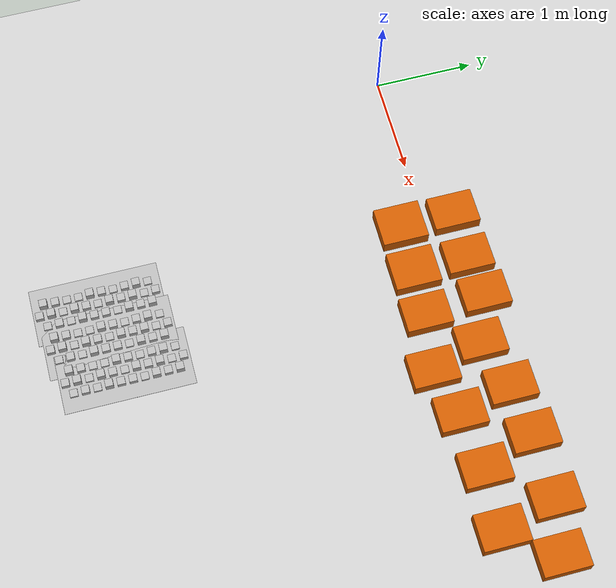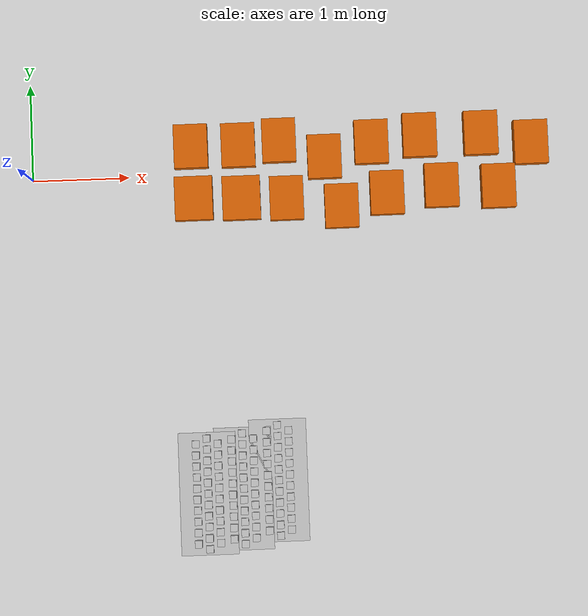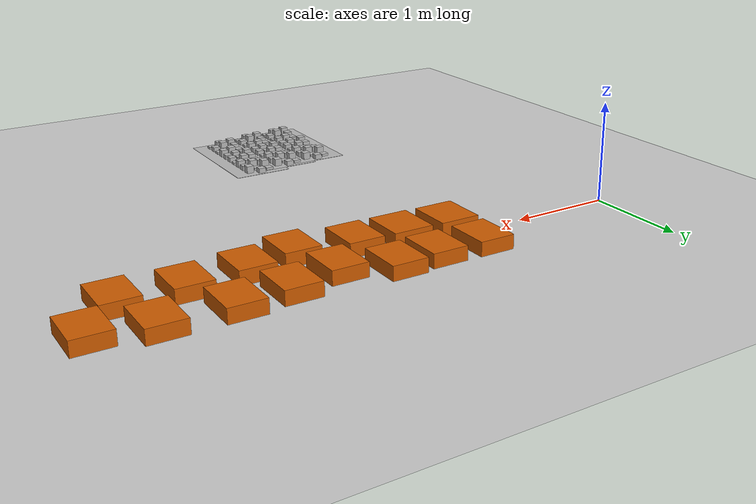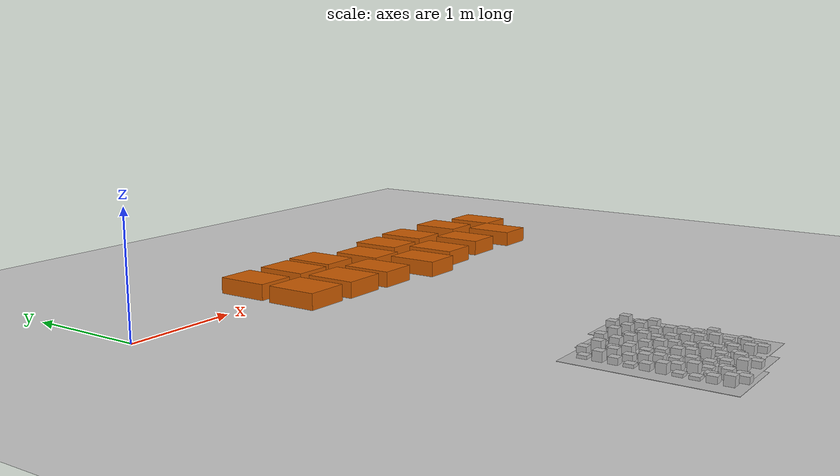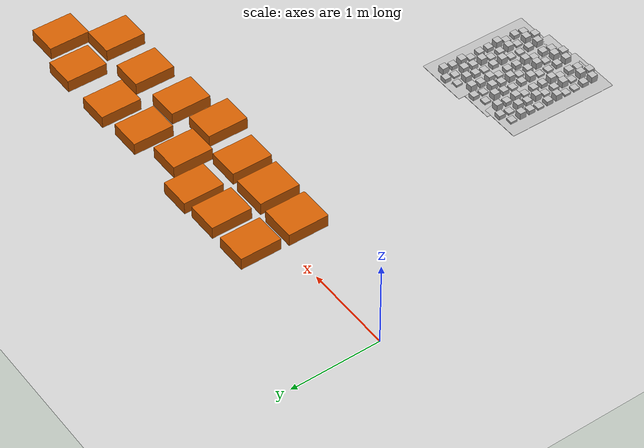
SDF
<sdf version="1.7">
 <world name="default">
  <light name="sun" type="directional">
   <pose>0 0 10 0 -0 0</pose>
   <diffuse>0.8 0.8 0.8 1</diffuse>
   <specular>0.1 0.1 0.1 1</specular>
   <attenuation>
    <range>1000</range>
    <constant>0.9</constant>
    <linear>0.01</linear>
    <quadratic>0.001</quadratic>
   </attenuation>
   <direction>-0.5 0.5 -1</direction>
   <spot><inner_angle>0</inner_angle><outer_angle>0</outer_angle><falloff>0</falloff></spot>
  </light>
  <model name="ground_plane">
   <static>1</static>
   <link name="link">
    <collision name="collision">
     <geometry><plane><normal>0 0 1</normal><size>100 100</size></plane></geometry>
     <surface><friction><ode><mu>100</mu><mu2>50</mu2></ode></friction></surface>
    </collision>
    <visual name="visual">
     <cast_shadows>0</cast_shadows>
     <geometry><plane><normal>0 0 1</normal><size>100 100</size></plane></geometry>
     <material>
      <script><uri>file://media/materials/scripts/gazebo.material</uri><name>Gazebo/Grey</name></script>
     </material>
    </visual>
   </link>
  </model>
  <gravity>0 0 -9.8</gravity>
  <magnetic_field>6e-06 2.3e-05 -4.2e-05</magnetic_field>
  <atmosphere type="adiabatic"/>
  <physics name="default_physics" default="0" type="ode">
   <max_step_size>0.001</max_step_size>
   <real_time_factor>1</real_time_factor>
   <real_time_update_rate>1000</real_time_update_rate>
  </physics>
  <scene><ambient>0.4 0.4 0.4 1</ambient><background>0.7 0.7 0.7 1</background><shadows>1</shadows></scene>
  <spherical_coordinates>
   <surface_model>EARTH_WGS84</surface_model>
   <latitude_deg>0</latitude_deg>
   <longitude_deg>0</longitude_deg>
   <elevation>0</elevation>
   <heading_deg>0</heading_deg>
  </spherical_coordinates>
  <model name="frc2016_roughterrain">
   <static>1</static>
   <link name="link">
    <visual name="platform">
     <pose>0 0 0.08269 0 -0 0</pose>
     <geometry><box><size>1.27 0.5969 0.003175</size></box></geometry>
    </visual>
    <collision name="platform">
     <pose>0 0 0.08269 0 -0 0</pose>
     <geometry><box><size>1.27 0.5969 0.003175</size></box></geometry>
    </collision>
    <visual name="row1_block1_sm">
     <pose>0.51435 0.1143 0.09698 0 -0 0</pose>
     <geometry><box><size>0.0762 0.0762 0.0254</size></box></geometry>
    </visual>
    <collision name="row1_block1_sm">
     <pose>0.51435 0.1143 0.09698 0 -0 0</pose>
     <geometry><box><size>0.0762 0.0762 0.0254</size></box></geometry>
    </collision>
    <visual name="row1_block2_lg">
     <pose>0.40005 0.1143 0.12238 0 -0 0</pose>
     <geometry><box><size>0.0762 0.0762 0.0762</size></box></geometry>
    </visual>
    <collision name="row1_block2_lg">
     <pose>0.40005 0.1143 0.12238 0 -0 0</pose>
     <geometry><box><size>0.0762 0.0762 0.0762</size></box></geometry>
    </collision>
    <visual name="row1_block3_md">
     <pose>0.28575 0.1143 0.10968 0 -0 0</pose>
     <geometry><box><size>0.0762 0.0762 0.0508</size></box></geometry>
    </visual>
    <collision name="row1_block3_md">
     <pose>0.28575 0.1143 0.10968 0 -0 0</pose>
     <geometry><box><size>0.0762 0.0762 0.0508</size></box></geometry>
    </collision>
    <visual name="row1_block4_sm">
     <pose>0.17145 0.1143 0.09698 0 -0 0</pose>
     <geometry><box><size>0.0762 0.0762 0.0254</size></box></geometry>
    </visual>
    <collision name="row1_block4_sm">
     <pose>0.17145 0.1143 0.09698 0 -0 0</pose>
     <geometry><box><size>0.0762 0.0762 0.0254</size></box></geometry>
    </collision>
    <visual name="row1_block5_md">
     <pose>0.05715 0.1143 0.10968 0 -0 0</pose>
     <geometry><box><size>0.0762 0.0762 0.0508</size></box></geometry>
    </visual>
    <collision name="row1_block5_md">
     <pose>0.05715 0.1143 0.10968 0 -0 0</pose>
     <geometry><box><size>0.0762 0.0762 0.0508</size></box></geometry>
    </collision>
    <visual name="row1_block6_lg">
     <pose>-0.05715 0.1143 0.12238 0 -0 0</pose>
     <geometry><box><size>0.0762 0.0762 0.0762</size></box></geometry>
    </visual>
    <collision name="row1_block6_lg">
     <pose>-0.05715 0.1143 0.12238 0 -0 0</pose>
     <geometry><box><size>0.0762 0.0762 0.0762</size></box></geometry>
    </collision>
    <visual name="row1_block7_sm">
     <pose>-0.17145 0.1143 0.09698 0 -0 0</pose>
     <geometry><box><size>0.0762 0.0762 0.0254</size></box></geometry>
    </visual>
    <collision name="row1_block7_sm">
     <pose>-0.17145 0.1143 0.09698 0 -0 0</pose>
     <geometry><box><size>0.0762 0.0762 0.0254</size></box></geometry>
    </collision>
    <visual name="row1_block8_sm">
     <pose>-0.28575 0.1143 0.09698 0 -0 0</pose>
     <geometry><box><size>0.0762 0.0762 0.0254</size></box></geometry>
    </visual>
    <collision name="row1_block8_sm">
     <pose>-0.28575 0.1143 0.09698 0 -0 0</pose>
     <geometry><box><size>0.0762 0.0762 0.0254</size></box></geometry>
    </collision>
    <visual name="row1_block9_md">
     <pose>-0.40005 0.1143 0.10968 0 -0 0</pose>
     <geometry><box><size>0.0762 0.0762 0.0508</size></box></geometry>
    </visual>
    <collision name="row1_block9_md">
     <pose>-0.40005 0.1143 0.10968 0 -0 0</pose>
     <geometry><box><size>0.0762 0.0762 0.0508</size></box></geometry>
    </collision>
    <visual name="row1_block10_lg">
     <pose>-0.51435 0.1143 0.12238 0 -0 0</pose>
     <geometry><box><size>0.0762 0.0762 0.0762</size></box></geometry>
    </visual>
    <collision name="row1_block10_lg">
     <pose>-0.51435 0.1143 0.12238 0 -0 0</pose>
     <geometry><box><size>0.0762 0.0762 0.0762</size></box></geometry>
    </collision>
    <visual name="row2_block1_md">
     <pose>0.5715 0 0.10968 0 -0 0</pose>
     <geometry><box><size>0.0762 0.0762 0.0508</size></box></geometry>
    </visual>
    <collision name="row2_block1_md">
     <pose>0.5715 0 0.10968 0 -0 0</pose>
     <geometry><box><size>0.0762 0.0762 0.0508</size></box></geometry>
    </collision>
    <visual name="row2_block2_sm">
     <pose>0.4572 0 0.09698 0 -0 0</pose>
     <geometry><box><size>0.0762 0.0762 0.0254</size></box></geometry>
    </visual>
    <collision name="row2_block2_sm">
     <pose>0.4572 0 0.09698 0 -0 0</pose>
     <geometry><box><size>0.0762 0.0762 0.0254</size></box></geometry>
    </collision>
    <visual name="row2_block3_lg">
     <pose>0.3429 0 0.12238 0 -0 0</pose>
     <geometry><box><size>0.0762 0.0762 0.0762</size></box></geometry>
    </visual>
    <collision name="row2_block3_lg">
     <pose>0.3429 0 0.12238 0 -0 0</pose>
     <geometry><box><size>0.0762 0.0762 0.0762</size></box></geometry>
    </collision>
    <visual name="row2_block4_md">
     <pose>0.2286 0 0.10968 0 -0 0</pose>
     <geometry><box><size>0.0762 0.0762 0.0508</size></box></geometry>
    </visual>
    <collision name="row2_block4_md">
     <pose>0.2286 0 0.10968 0 -0 0</pose>
     <geometry><box><size>0.0762 0.0762 0.0508</size></box></geometry>
    </collision>
    <visual name="row2_block5_lg">
     <pose>0.1143 0 0.12238 0 -0 0</pose>
     <geometry><box><size>0.0762 0.0762 0.0762</size></box></geometry>
    </visual>
    <collision name="row2_block5_lg">
     <pose>0.1143 0 0.12238 0 -0 0</pose>
     <geometry><box><size>0.0762 0.0762 0.0762</size></box></geometry>
    </collision>
    <visual name="row2_block6_sm">
     <pose>0 0 0.09698 0 -0 0</pose>
     <geometry><box><size>0.0762 0.0762 0.0254</size></box></geometry>
    </visual>
    <collision name="row2_block6_sm">
     <pose>0 0 0.09698 0 -0 0</pose>
     <geometry><box><size>0.0762 0.0762 0.0254</size></box></geometry>
    </collision>
    <visual name="row2_block7_md">
     <pose>-0.1143 0 0.10968 0 -0 0</pose>
     <geometry><box><size>0.0762 0.0762 0.0508</size></box></geometry>
    </visual>
    <collision name="row2_block7_md">
     <pose>-0.1143 0 0.10968 0 -0 0</pose>
     <geometry><box><size>0.0762 0.0762 0.0508</size></box></geometry>
    </collision>
    <visual name="row2_block8_lg">
     <pose>-0.2286 0 0.12238 0 -0 0</pose>
     <geometry><box><size>0.0762 0.0762 0.0762</size></box></geometry>
    </visual>
    <collision name="row2_block8_lg">
     <pose>-0.2286 0 0.12238 0 -0 0</pose>
     <geometry><box><size>0.0762 0.0762 0.0762</size></box></geometry>
    </collision>
    <visual name="row2_block9_sm">
     <pose>-0.3429 0 0.09698 0 -0 0</pose>
     <geometry><box><size>0.0762 0.0762 0.0254</size></box></geometry>
    </visual>
    <collision name="row2_block9_sm">
     <pose>-0.3429 0 0.09698 0 -0 0</pose>
     <geometry><box><size>0.0762 0.0762 0.0254</size></box></geometry>
    </collision>
    <visual name="row2_block10_lg">
     <pose>-0.4572 0 0.12238 0 -0 0</pose>
     <geometry><box><size>0.0762 0.0762 0.0762</size></box></geometry>
    </visual>
    <collision name="row2_block10_lg">
     <pose>-0.4572 0 0.12238 0 -0 0</pose>
     <geometry><box><size>0.0762 0.0762 0.0762</size></box></geometry>
    </collision>
    <visual name="row2_block11_md">
     <pose>-0.5715 0 0.10968 0 -0 0</pose>
     <geometry><box><size>0.0762 0.0762 0.0508</size></box></geometry>
    </visual>
    <collision name="row2_block11_md">
     <pose>-0.5715 0 0.10968 0 -0 0</pose>
     <geometry><box><size>0.0762 0.0762 0.0508</size></box></geometry>
    </collision>
    <visual name="row3_block1_lg">
     <pose>0.51435 -0.1143 0.12238 0 -0 0</pose>
     <geometry><box><size>0.0762 0.0762 0.0762</size></box></geometry>
    </visual>
    <collision name="row3_block1_lg">
     <pose>0.51435 -0.1143 0.12238 0 -0 0</pose>
     <geometry><box><size>0.0762 0.0762 0.0762</size></box></geometry>
    </collision>
    <visual name="row3_block2_md">
     <pose>0.40005 -0.1143 0.10968 0 -0 0</pose>
     <geometry><box><size>0.0762 0.0762 0.0508</size></box></geometry>
    </visual>
    <collision name="row3_block2_md">
     <pose>0.40005 -0.1143 0.10968 0 -0 0</pose>
     <geometry><box><size>0.0762 0.0762 0.0508</size></box></geometry>
    </collision>
    <visual name="row3_block3_lg">
     <pose>0.28575 -0.1143 0.12238 0 -0 0</pose>
     <geometry><box><size>0.0762 0.0762 0.0762</size></box></geometry>
    </visual>
    <collision name="row3_block3_lg">
     <pose>0.28575 -0.1143 0.12238 0 -0 0</pose>
     <geometry><box><size>0.0762 0.0762 0.0762</size></box></geometry>
    </collision>
    <visual name="row3_block4_sm">
     <pose>0.17145 -0.1143 0.09698 0 -0 0</pose>
     <geometry><box><size>0.0762 0.0762 0.0254</size></box></geometry>
    </visual>
    <collision name="row3_block4_sm">
     <pose>0.17145 -0.1143 0.09698 0 -0 0</pose>
     <geometry><box><size>0.0762 0.0762 0.0254</size></box></geometry>
    </collision>
    <visual name="row3_block5_md">
     <pose>0.05715 -0.1143 0.10968 0 -0 0</pose>
     <geometry><box><size>0.0762 0.0762 0.0508</size></box></geometry>
    </visual>
    <collision name="row3_block5_md">
     <pose>0.05715 -0.1143 0.10968 0 -0 0</pose>
     <geometry><box><size>0.0762 0.0762 0.0508</size></box></geometry>
    </collision>
    <visual name="row3_block6_md">
     <pose>-0.05715 -0.1143 0.10968 0 -0 0</pose>
     <geometry><box><size>0.0762 0.0762 0.0508</size></box></geometry>
    </visual>
    <collision name="row3_block6_md">
     <pose>-0.05715 -0.1143 0.10968 0 -0 0</pose>
     <geometry><box><size>0.0762 0.0762 0.0508</size></box></geometry>
    </collision>
    <visual name="row3_block7_lg">
     <pose>-0.17145 -0.1143 0.12238 0 -0 0</pose>
     <geometry><box><size>0.0762 0.0762 0.0762</size></box></geometry>
    </visual>
    <collision name="row3_block7_lg">
     <pose>-0.17145 -0.1143 0.12238 0 -0 0</pose>
     <geometry><box><size>0.0762 0.0762 0.0762</size></box></geometry>
    </collision>
    <visual name="row3_block8_sm">
     <pose>-0.28575 -0.1143 0.09698 0 -0 0</pose>
     <geometry><box><size>0.0762 0.0762 0.0254</size></box></geometry>
    </visual>
    <collision name="row3_block8_sm">
     <pose>-0.28575 -0.1143 0.09698 0 -0 0</pose>
     <geometry><box><size>0.0762 0.0762 0.0254</size></box></geometry>
    </collision>
    <visual name="row3_block9_md">
     <pose>-0.40005 -0.1143 0.10968 0 -0 0</pose>
     <geometry><box><size>0.0762 0.0762 0.0508</size></box></geometry>
    </visual>
    <collision name="row3_block9_md">
     <pose>-0.40005 -0.1143 0.10968 0 -0 0</pose>
     <geometry><box><size>0.0762 0.0762 0.0508</size></box></geometry>
    </collision>
    <visual name="row3_block10_sm">
     <pose>-0.51435 -0.1143 0.09698 0 -0 0</pose>
     <geometry><box><size>0.0762 0.0762 0.0254</size></box></geometry>
    </visual>
    <collision name="row3_block10_sm">
     <pose>-0.51435 -0.1143 0.09698 0 -0 0</pose>
     <geometry><box><size>0.0762 0.0762 0.0254</size></box></geometry>
    </collision>
   </link>
   <pose>1.70324 -3.32243 -0.086398 0 -0 1.56747</pose>
  </model>
  <model name="frc2016_roughterrain_clone">
   <static>1</static>
   <link name="link">
    <visual name="platform">
     <pose>0 0 0.08269 0 -0 0</pose>
     <geometry><box><size>1.27 0.5969 0.003175</size></box></geometry>
    </visual>
    <collision name="platform">
     <pose>0 0 0.08269 0 -0 0</pose>
     <geometry><box><size>1.27 0.5969 0.003175</size></box></geometry>
    </collision>
    <visual name="row1_block1_sm">
     <pose>0.51435 0.1143 0.09698 0 -0 0</pose>
     <geometry><box><size>0.0762 0.0762 0.0254</size></box></geometry>
    </visual>
    <collision name="row1_block1_sm">
     <pose>0.51435 0.1143 0.09698 0 -0 0</pose>
     <geometry><box><size>0.0762 0.0762 0.0254</size></box></geometry>
    </collision>
    <visual name="row1_block2_lg">
     <pose>0.40005 0.1143 0.12238 0 -0 0</pose>
     <geometry><box><size>0.0762 0.0762 0.0762</size></box></geometry>
    </visual>
    <collision name="row1_block2_lg">
     <pose>0.40005 0.1143 0.12238 0 -0 0</pose>
     <geometry><box><size>0.0762 0.0762 0.0762</size></box></geometry>
    </collision>
    <visual name="row1_block3_md">
     <pose>0.28575 0.1143 0.10968 0 -0 0</pose>
     <geometry><box><size>0.0762 0.0762 0.0508</size></box></geometry>
    </visual>
    <collision name="row1_block3_md">
     <pose>0.28575 0.1143 0.10968 0 -0 0</pose>
     <geometry><box><size>0.0762 0.0762 0.0508</size></box></geometry>
    </collision>
    <visual name="row1_block4_sm">
     <pose>0.17145 0.1143 0.09698 0 -0 0</pose>
     <geometry><box><size>0.0762 0.0762 0.0254</size></box></geometry>
    </visual>
    <collision name="row1_block4_sm">
     <pose>0.17145 0.1143 0.09698 0 -0 0</pose>
     <geometry><box><size>0.0762 0.0762 0.0254</size></box></geometry>
    </collision>
    <visual name="row1_block5_md">
     <pose>0.05715 0.1143 0.10968 0 -0 0</pose>
     <geometry><box><size>0.0762 0.0762 0.0508</size></box></geometry>
    </visual>
    <collision name="row1_block5_md">
     <pose>0.05715 0.1143 0.10968 0 -0 0</pose>
     <geometry><box><size>0.0762 0.0762 0.0508</size></box></geometry>
    </collision>
    <visual name="row1_block6_lg">
     <pose>-0.05715 0.1143 0.12238 0 -0 0</pose>
     <geometry><box><size>0.0762 0.0762 0.0762</size></box></geometry>
    </visual>
    <collision name="row1_block6_lg">
     <pose>-0.05715 0.1143 0.12238 0 -0 0</pose>
     <geometry><box><size>0.0762 0.0762 0.0762</size></box></geometry>
    </collision>
    <visual name="row1_block7_sm">
     <pose>-0.17145 0.1143 0.09698 0 -0 0</pose>
     <geometry><box><size>0.0762 0.0762 0.0254</size></box></geometry>
    </visual>
    <collision name="row1_block7_sm">
     <pose>-0.17145 0.1143 0.09698 0 -0 0</pose>
     <geometry><box><size>0.0762 0.0762 0.0254</size></box></geometry>
    </collision>
    <visual name="row1_block8_sm">
     <pose>-0.28575 0.1143 0.09698 0 -0 0</pose>
     <geometry><box><size>0.0762 0.0762 0.0254</size></box></geometry>
    </visual>
    <collision name="row1_block8_sm">
     <pose>-0.28575 0.1143 0.09698 0 -0 0</pose>
     <geometry><box><size>0.0762 0.0762 0.0254</size></box></geometry>
    </collision>
    <visual name="row1_block9_md">
     <pose>-0.40005 0.1143 0.10968 0 -0 0</pose>
     <geometry><box><size>0.0762 0.0762 0.0508</size></box></geometry>
    </visual>
    <collision name="row1_block9_md">
     <pose>-0.40005 0.1143 0.10968 0 -0 0</pose>
     <geometry><box><size>0.0762 0.0762 0.0508</size></box></geometry>
    </collision>
    <visual name="row1_block10_lg">
     <pose>-0.51435 0.1143 0.12238 0 -0 0</pose>
     <geometry><box><size>0.0762 0.0762 0.0762</size></box></geometry>
    </visual>
    <collision name="row1_block10_lg">
     <pose>-0.51435 0.1143 0.12238 0 -0 0</pose>
     <geometry><box><size>0.0762 0.0762 0.0762</size></box></geometry>
    </collision>
    <visual name="row2_block1_md">
     <pose>0.5715 0 0.10968 0 -0 0</pose>
     <geometry><box><size>0.0762 0.0762 0.0508</size></box></geometry>
    </visual>
    <collision name="row2_block1_md">
     <pose>0.5715 0 0.10968 0 -0 0</pose>
     <geometry><box><size>0.0762 0.0762 0.0508</size></box></geometry>
    </collision>
    <visual name="row2_block2_sm">
     <pose>0.4572 0 0.09698 0 -0 0</pose>
     <geometry><box><size>0.0762 0.0762 0.0254</size></box></geometry>
    </visual>
    <collision name="row2_block2_sm">
     <pose>0.4572 0 0.09698 0 -0 0</pose>
     <geometry><box><size>0.0762 0.0762 0.0254</size></box></geometry>
    </collision>
    <visual name="row2_block3_lg">
     <pose>0.3429 0 0.12238 0 -0 0</pose>
     <geometry><box><size>0.0762 0.0762 0.0762</size></box></geometry>
    </visual>
    <collision name="row2_block3_lg">
     <pose>0.3429 0 0.12238 0 -0 0</pose>
     <geometry><box><size>0.0762 0.0762 0.0762</size></box></geometry>
    </collision>
    <visual name="row2_block4_md">
     <pose>0.2286 0 0.10968 0 -0 0</pose>
     <geometry><box><size>0.0762 0.0762 0.0508</size></box></geometry>
    </visual>
    <collision name="row2_block4_md">
     <pose>0.2286 0 0.10968 0 -0 0</pose>
     <geometry><box><size>0.0762 0.0762 0.0508</size></box></geometry>
    </collision>
    <visual name="row2_block5_lg">
     <pose>0.1143 0 0.12238 0 -0 0</pose>
     <geometry><box><size>0.0762 0.0762 0.0762</size></box></geometry>
    </visual>
    <collision name="row2_block5_lg">
     <pose>0.1143 0 0.12238 0 -0 0</pose>
     <geometry><box><size>0.0762 0.0762 0.0762</size></box></geometry>
    </collision>
    <visual name="row2_block6_sm">
     <pose>0 0 0.09698 0 -0 0</pose>
     <geometry><box><size>0.0762 0.0762 0.0254</size></box></geometry>
    </visual>
    <collision name="row2_block6_sm">
     <pose>0 0 0.09698 0 -0 0</pose>
     <geometry><box><size>0.0762 0.0762 0.0254</size></box></geometry>
    </collision>
    <visual name="row2_block7_md">
     <pose>-0.1143 0 0.10968 0 -0 0</pose>
     <geometry><box><size>0.0762 0.0762 0.0508</size></box></geometry>
    </visual>
    <collision name="row2_block7_md">
     <pose>-0.1143 0 0.10968 0 -0 0</pose>
     <geometry><box><size>0.0762 0.0762 0.0508</size></box></geometry>
    </collision>
    <visual name="row2_block8_lg">
     <pose>-0.2286 0 0.12238 0 -0 0</pose>
     <geometry><box><size>0.0762 0.0762 0.0762</size></box></geometry>
    </visual>
    <collision name="row2_block8_lg">
     <pose>-0.2286 0 0.12238 0 -0 0</pose>
     <geometry><box><size>0.0762 0.0762 0.0762</size></box></geometry>
    </collision>
    <visual name="row2_block9_sm">
     <pose>-0.3429 0 0.09698 0 -0 0</pose>
     <geometry><box><size>0.0762 0.0762 0.0254</size></box></geometry>
    </visual>
    <collision name="row2_block9_sm">
     <pose>-0.3429 0 0.09698 0 -0 0</pose>
     <geometry><box><size>0.0762 0.0762 0.0254</size></box></geometry>
    </collision>
    <visual name="row2_block10_lg">
     <pose>-0.4572 0 0.12238 0 -0 0</pose>
     <geometry><box><size>0.0762 0.0762 0.0762</size></box></geometry>
    </visual>
    <collision name="row2_block10_lg">
     <pose>-0.4572 0 0.12238 0 -0 0</pose>
     <geometry><box><size>0.0762 0.0762 0.0762</size></box></geometry>
    </collision>
    <visual name="row2_block11_md">
     <pose>-0.5715 0 0.10968 0 -0 0</pose>
     <geometry><box><size>0.0762 0.0762 0.0508</size></box></geometry>
    </visual>
    <collision name="row2_block11_md">
     <pose>-0.5715 0 0.10968 0 -0 0</pose>
     <geometry><box><size>0.0762 0.0762 0.0508</size></box></geometry>
    </collision>
    <visual name="row3_block1_lg">
     <pose>0.51435 -0.1143 0.12238 0 -0 0</pose>
     <geometry><box><size>0.0762 0.0762 0.0762</size></box></geometry>
    </visual>
    <collision name="row3_block1_lg">
     <pose>0.51435 -0.1143 0.12238 0 -0 0</pose>
     <geometry><box><size>0.0762 0.0762 0.0762</size></box></geometry>
    </collision>
    <visual name="row3_block2_md">
     <pose>0.40005 -0.1143 0.10968 0 -0 0</pose>
     <geometry><box><size>0.0762 0.0762 0.0508</size></box></geometry>
    </visual>
    <collision name="row3_block2_md">
     <pose>0.40005 -0.1143 0.10968 0 -0 0</pose>
     <geometry><box><size>0.0762 0.0762 0.0508</size></box></geometry>
    </collision>
    <visual name="row3_block3_lg">
     <pose>0.28575 -0.1143 0.12238 0 -0 0</pose>
     <geometry><box><size>0.0762 0.0762 0.0762</size></box></geometry>
    </visual>
    <collision name="row3_block3_lg">
     <pose>0.28575 -0.1143 0.12238 0 -0 0</pose>
     <geometry><box><size>0.0762 0.0762 0.0762</size></box></geometry>
    </collision>
    <visual name="row3_block4_sm">
     <pose>0.17145 -0.1143 0.09698 0 -0 0</pose>
     <geometry><box><size>0.0762 0.0762 0.0254</size></box></geometry>
    </visual>
    <collision name="row3_block4_sm">
     <pose>0.17145 -0.1143 0.09698 0 -0 0</pose>
     <geometry><box><size>0.0762 0.0762 0.0254</size></box></geometry>
    </collision>
    <visual name="row3_block5_md">
     <pose>0.05715 -0.1143 0.10968 0 -0 0</pose>
     <geometry><box><size>0.0762 0.0762 0.0508</size></box></geometry>
    </visual>
    <collision name="row3_block5_md">
     <pose>0.05715 -0.1143 0.10968 0 -0 0</pose>
     <geometry><box><size>0.0762 0.0762 0.0508</size></box></geometry>
    </collision>
    <visual name="row3_block6_md">
     <pose>-0.05715 -0.1143 0.10968 0 -0 0</pose>
     <geometry><box><size>0.0762 0.0762 0.0508</size></box></geometry>
    </visual>
    <collision name="row3_block6_md">
     <pose>-0.05715 -0.1143 0.10968 0 -0 0</pose>
     <geometry><box><size>0.0762 0.0762 0.0508</size></box></geometry>
    </collision>
    <visual name="row3_block7_lg">
     <pose>-0.17145 -0.1143 0.12238 0 -0 0</pose>
     <geometry><box><size>0.0762 0.0762 0.0762</size></box></geometry>
    </visual>
    <collision name="row3_block7_lg">
     <pose>-0.17145 -0.1143 0.12238 0 -0 0</pose>
     <geometry><box><size>0.0762 0.0762 0.0762</size></box></geometry>
    </collision>
    <visual name="row3_block8_sm">
     <pose>-0.28575 -0.1143 0.09698 0 -0 0</pose>
     <geometry><box><size>0.0762 0.0762 0.0254</size></box></geometry>
    </visual>
    <collision name="row3_block8_sm">
     <pose>-0.28575 -0.1143 0.09698 0 -0 0</pose>
     <geometry><box><size>0.0762 0.0762 0.0254</size></box></geometry>
    </collision>
    <visual name="row3_block9_md">
     <pose>-0.40005 -0.1143 0.10968 0 -0 0</pose>
     <geometry><box><size>0.0762 0.0762 0.0508</size></box></geometry>
    </visual>
    <collision name="row3_block9_md">
     <pose>-0.40005 -0.1143 0.10968 0 -0 0</pose>
     <geometry><box><size>0.0762 0.0762 0.0508</size></box></geometry>
    </collision>
    <visual name="row3_block10_sm">
     <pose>-0.51435 -0.1143 0.09698 0 -0 0</pose>
     <geometry><box><size>0.0762 0.0762 0.0254</size></box></geometry>
    </visual>
    <collision name="row3_block10_sm">
     <pose>-0.51435 -0.1143 0.09698 0 -0 0</pose>
     <geometry><box><size>0.0762 0.0762 0.0254</size></box></geometry>
    </collision>
   </link>
   <pose>2.07302 -3.28394 -0.086398 0 -0 1.56747</pose>
  </model>
  <model name="frc2016_roughterrain_clone_0">
   <static>1</static>
   <link name="link">
    <visual name="platform">
     <pose>0 0 0.08269 0 -0 0</pose>
     <geometry><box><size>1.27 0.5969 0.003175</size></box></geometry>
    </visual>
    <collision name="platform">
     <pose>0 0 0.08269 0 -0 0</pose>
     <geometry><box><size>1.27 0.5969 0.003175</size></box></geometry>
    </collision>
    <visual name="row1_block1_sm">
     <pose>0.51435 0.1143 0.09698 0 -0 0</pose>
     <geometry><box><size>0.0762 0.0762 0.0254</size></box></geometry>
    </visual>
    <collision name="row1_block1_sm">
     <pose>0.51435 0.1143 0.09698 0 -0 0</pose>
     <geometry><box><size>0.0762 0.0762 0.0254</size></box></geometry>
    </collision>
    <visual name="row1_block2_lg">
     <pose>0.40005 0.1143 0.12238 0 -0 0</pose>
     <geometry><box><size>0.0762 0.0762 0.0762</size></box></geometry>
    </visual>
    <collision name="row1_block2_lg">
     <pose>0.40005 0.1143 0.12238 0 -0 0</pose>
     <geometry><box><size>0.0762 0.0762 0.0762</size></box></geometry>
    </collision>
    <visual name="row1_block3_md">
     <pose>0.28575 0.1143 0.10968 0 -0 0</pose>
     <geometry><box><size>0.0762 0.0762 0.0508</size></box></geometry>
    </visual>
    <collision name="row1_block3_md">
     <pose>0.28575 0.1143 0.10968 0 -0 0</pose>
     <geometry><box><size>0.0762 0.0762 0.0508</size></box></geometry>
    </collision>
    <visual name="row1_block4_sm">
     <pose>0.17145 0.1143 0.09698 0 -0 0</pose>
     <geometry><box><size>0.0762 0.0762 0.0254</size></box></geometry>
    </visual>
    <collision name="row1_block4_sm">
     <pose>0.17145 0.1143 0.09698 0 -0 0</pose>
     <geometry><box><size>0.0762 0.0762 0.0254</size></box></geometry>
    </collision>
    <visual name="row1_block5_md">
     <pose>0.05715 0.1143 0.10968 0 -0 0</pose>
     <geometry><box><size>0.0762 0.0762 0.0508</size></box></geometry>
    </visual>
    <collision name="row1_block5_md">
     <pose>0.05715 0.1143 0.10968 0 -0 0</pose>
     <geometry><box><size>0.0762 0.0762 0.0508</size></box></geometry>
    </collision>
    <visual name="row1_block6_lg">
     <pose>-0.05715 0.1143 0.12238 0 -0 0</pose>
     <geometry><box><size>0.0762 0.0762 0.0762</size></box></geometry>
    </visual>
    <collision name="row1_block6_lg">
     <pose>-0.05715 0.1143 0.12238 0 -0 0</pose>
     <geometry><box><size>0.0762 0.0762 0.0762</size></box></geometry>
    </collision>
    <visual name="row1_block7_sm">
     <pose>-0.17145 0.1143 0.09698 0 -0 0</pose>
     <geometry><box><size>0.0762 0.0762 0.0254</size></box></geometry>
    </visual>
    <collision name="row1_block7_sm">
     <pose>-0.17145 0.1143 0.09698 0 -0 0</pose>
     <geometry><box><size>0.0762 0.0762 0.0254</size></box></geometry>
    </collision>
    <visual name="row1_block8_sm">
     <pose>-0.28575 0.1143 0.09698 0 -0 0</pose>
     <geometry><box><size>0.0762 0.0762 0.0254</size></box></geometry>
    </visual>
    <collision name="row1_block8_sm">
     <pose>-0.28575 0.1143 0.09698 0 -0 0</pose>
     <geometry><box><size>0.0762 0.0762 0.0254</size></box></geometry>
    </collision>
    <visual name="row1_block9_md">
     <pose>-0.40005 0.1143 0.10968 0 -0 0</pose>
     <geometry><box><size>0.0762 0.0762 0.0508</size></box></geometry>
    </visual>
    <collision name="row1_block9_md">
     <pose>-0.40005 0.1143 0.10968 0 -0 0</pose>
     <geometry><box><size>0.0762 0.0762 0.0508</size></box></geometry>
    </collision>
    <visual name="row1_block10_lg">
     <pose>-0.51435 0.1143 0.12238 0 -0 0</pose>
     <geometry><box><size>0.0762 0.0762 0.0762</size></box></geometry>
    </visual>
    <collision name="row1_block10_lg">
     <pose>-0.51435 0.1143 0.12238 0 -0 0</pose>
     <geometry><box><size>0.0762 0.0762 0.0762</size></box></geometry>
    </collision>
    <visual name="row2_block1_md">
     <pose>0.5715 0 0.10968 0 -0 0</pose>
     <geometry><box><size>0.0762 0.0762 0.0508</size></box></geometry>
    </visual>
    <collision name="row2_block1_md">
     <pose>0.5715 0 0.10968 0 -0 0</pose>
     <geometry><box><size>0.0762 0.0762 0.0508</size></box></geometry>
    </collision>
    <visual name="row2_block2_sm">
     <pose>0.4572 0 0.09698 0 -0 0</pose>
     <geometry><box><size>0.0762 0.0762 0.0254</size></box></geometry>
    </visual>
    <collision name="row2_block2_sm">
     <pose>0.4572 0 0.09698 0 -0 0</pose>
     <geometry><box><size>0.0762 0.0762 0.0254</size></box></geometry>
    </collision>
    <visual name="row2_block3_lg">
     <pose>0.3429 0 0.12238 0 -0 0</pose>
     <geometry><box><size>0.0762 0.0762 0.0762</size></box></geometry>
    </visual>
    <collision name="row2_block3_lg">
     <pose>0.3429 0 0.12238 0 -0 0</pose>
     <geometry><box><size>0.0762 0.0762 0.0762</size></box></geometry>
    </collision>
    <visual name="row2_block4_md">
     <pose>0.2286 0 0.10968 0 -0 0</pose>
     <geometry><box><size>0.0762 0.0762 0.0508</size></box></geometry>
    </visual>
    <collision name="row2_block4_md">
     <pose>0.2286 0 0.10968 0 -0 0</pose>
     <geometry><box><size>0.0762 0.0762 0.0508</size></box></geometry>
    </collision>
    <visual name="row2_block5_lg">
     <pose>0.1143 0 0.12238 0 -0 0</pose>
     <geometry><box><size>0.0762 0.0762 0.0762</size></box></geometry>
    </visual>
    <collision name="row2_block5_lg">
     <pose>0.1143 0 0.12238 0 -0 0</pose>
     <geometry><box><size>0.0762 0.0762 0.0762</size></box></geometry>
    </collision>
    <visual name="row2_block6_sm">
     <pose>0 0 0.09698 0 -0 0</pose>
     <geometry><box><size>0.0762 0.0762 0.0254</size></box></geometry>
    </visual>
    <collision name="row2_block6_sm">
     <pose>0 0 0.09698 0 -0 0</pose>
     <geometry><box><size>0.0762 0.0762 0.0254</size></box></geometry>
    </collision>
    <visual name="row2_block7_md">
     <pose>-0.1143 0 0.10968 0 -0 0</pose>
     <geometry><box><size>0.0762 0.0762 0.0508</size></box></geometry>
    </visual>
    <collision name="row2_block7_md">
     <pose>-0.1143 0 0.10968 0 -0 0</pose>
     <geometry><box><size>0.0762 0.0762 0.0508</size></box></geometry>
    </collision>
    <visual name="row2_block8_lg">
     <pose>-0.2286 0 0.12238 0 -0 0</pose>
     <geometry><box><size>0.0762 0.0762 0.0762</size></box></geometry>
    </visual>
    <collision name="row2_block8_lg">
     <pose>-0.2286 0 0.12238 0 -0 0</pose>
     <geometry><box><size>0.0762 0.0762 0.0762</size></box></geometry>
    </collision>
    <visual name="row2_block9_sm">
     <pose>-0.3429 0 0.09698 0 -0 0</pose>
     <geometry><box><size>0.0762 0.0762 0.0254</size></box></geometry>
    </visual>
    <collision name="row2_block9_sm">
     <pose>-0.3429 0 0.09698 0 -0 0</pose>
     <geometry><box><size>0.0762 0.0762 0.0254</size></box></geometry>
    </collision>
    <visual name="row2_block10_lg">
     <pose>-0.4572 0 0.12238 0 -0 0</pose>
     <geometry><box><size>0.0762 0.0762 0.0762</size></box></geometry>
    </visual>
    <collision name="row2_block10_lg">
     <pose>-0.4572 0 0.12238 0 -0 0</pose>
     <geometry><box><size>0.0762 0.0762 0.0762</size></box></geometry>
    </collision>
    <visual name="row2_block11_md">
     <pose>-0.5715 0 0.10968 0 -0 0</pose>
     <geometry><box><size>0.0762 0.0762 0.0508</size></box></geometry>
    </visual>
    <collision name="row2_block11_md">
     <pose>-0.5715 0 0.10968 0 -0 0</pose>
     <geometry><box><size>0.0762 0.0762 0.0508</size></box></geometry>
    </collision>
    <visual name="row3_block1_lg">
     <pose>0.51435 -0.1143 0.12238 0 -0 0</pose>
     <geometry><box><size>0.0762 0.0762 0.0762</size></box></geometry>
    </visual>
    <collision name="row3_block1_lg">
     <pose>0.51435 -0.1143 0.12238 0 -0 0</pose>
     <geometry><box><size>0.0762 0.0762 0.0762</size></box></geometry>
    </collision>
    <visual name="row3_block2_md">
     <pose>0.40005 -0.1143 0.10968 0 -0 0</pose>
     <geometry><box><size>0.0762 0.0762 0.0508</size></box></geometry>
    </visual>
    <collision name="row3_block2_md">
     <pose>0.40005 -0.1143 0.10968 0 -0 0</pose>
     <geometry><box><size>0.0762 0.0762 0.0508</size></box></geometry>
    </collision>
    <visual name="row3_block3_lg">
     <pose>0.28575 -0.1143 0.12238 0 -0 0</pose>
     <geometry><box><size>0.0762 0.0762 0.0762</size></box></geometry>
    </visual>
    <collision name="row3_block3_lg">
     <pose>0.28575 -0.1143 0.12238 0 -0 0</pose>
     <geometry><box><size>0.0762 0.0762 0.0762</size></box></geometry>
    </collision>
    <visual name="row3_block4_sm">
     <pose>0.17145 -0.1143 0.09698 0 -0 0</pose>
     <geometry><box><size>0.0762 0.0762 0.0254</size></box></geometry>
    </visual>
    <collision name="row3_block4_sm">
     <pose>0.17145 -0.1143 0.09698 0 -0 0</pose>
     <geometry><box><size>0.0762 0.0762 0.0254</size></box></geometry>
    </collision>
    <visual name="row3_block5_md">
     <pose>0.05715 -0.1143 0.10968 0 -0 0</pose>
     <geometry><box><size>0.0762 0.0762 0.0508</size></box></geometry>
    </visual>
    <collision name="row3_block5_md">
     <pose>0.05715 -0.1143 0.10968 0 -0 0</pose>
     <geometry><box><size>0.0762 0.0762 0.0508</size></box></geometry>
    </collision>
    <visual name="row3_block6_md">
     <pose>-0.05715 -0.1143 0.10968 0 -0 0</pose>
     <geometry><box><size>0.0762 0.0762 0.0508</size></box></geometry>
    </visual>
    <collision name="row3_block6_md">
     <pose>-0.05715 -0.1143 0.10968 0 -0 0</pose>
     <geometry><box><size>0.0762 0.0762 0.0508</size></box></geometry>
    </collision>
    <visual name="row3_block7_lg">
     <pose>-0.17145 -0.1143 0.12238 0 -0 0</pose>
     <geometry><box><size>0.0762 0.0762 0.0762</size></box></geometry>
    </visual>
    <collision name="row3_block7_lg">
     <pose>-0.17145 -0.1143 0.12238 0 -0 0</pose>
     <geometry><box><size>0.0762 0.0762 0.0762</size></box></geometry>
    </collision>
    <visual name="row3_block8_sm">
     <pose>-0.28575 -0.1143 0.09698 0 -0 0</pose>
     <geometry><box><size>0.0762 0.0762 0.0254</size></box></geometry>
    </visual>
    <collision name="row3_block8_sm">
     <pose>-0.28575 -0.1143 0.09698 0 -0 0</pose>
     <geometry><box><size>0.0762 0.0762 0.0254</size></box></geometry>
    </collision>
    <visual name="row3_block9_md">
     <pose>-0.40005 -0.1143 0.10968 0 -0 0</pose>
     <geometry><box><size>0.0762 0.0762 0.0508</size></box></geometry>
    </visual>
    <collision name="row3_block9_md">
     <pose>-0.40005 -0.1143 0.10968 0 -0 0</pose>
     <geometry><box><size>0.0762 0.0762 0.0508</size></box></geometry>
    </collision>
    <visual name="row3_block10_sm">
     <pose>-0.51435 -0.1143 0.09698 0 -0 0</pose>
     <geometry><box><size>0.0762 0.0762 0.0254</size></box></geometry>
    </visual>
    <collision name="row3_block10_sm">
     <pose>-0.51435 -0.1143 0.09698 0 -0 0</pose>
     <geometry><box><size>0.0762 0.0762 0.0254</size></box></geometry>
    </collision>
   </link>
   <pose>2.4407 -3.2123 -0.086398 0 -0 1.56747</pose>
  </model>
  <model name="unit_box_clone">
   <link name="link">
    <inertial>
     <mass>1</mass>
     <inertia>
      <ixx>0.166667</ixx>
      <ixy>0</ixy>
      <ixz>0</ixz>
      <iyy>0.166667</iyy>
      <iyz>0</iyz>
      <izz>0.166667</izz>
     </inertia>
    </inertial>
    <visual name="visual">
     <geometry><box><size>0.394525 0.456132 0.142491</size></box></geometry>
     <material>
      <script><name>Gazebo/Grey</name><uri>file://media/materials/scripts/gazebo.material</uri></script>
      <shader type="pixel"><normal_map>__default__</normal_map></shader>
      <ambient>0.808 0.361 0 1</ambient>
      <diffuse>0.808 0.361 0 1</diffuse>
      <specular>0.808 0.361 0 1</specular>
      <emissive>0.808 0.361 0 1</emissive>
     </material>
    </visual>
    <collision name="collision">
     <geometry><box><size>0.394525 0.456132 0.142491</size></box></geometry>
     <surface>
      <friction>
       <ode><mu>1</mu><mu2>1</mu2><fdir1>0 0 0</fdir1><slip1>0</slip1><slip2>0</slip2></ode>
       <torsional>
        <coefficient>1</coefficient>
        <patch_radius>0</patch_radius>
        <surface_radius>0</surface_radius>
        <use_patch_radius>1</use_patch_radius>
        <ode><slip>0</slip></ode>
       </torsional>
      </friction>
      <bounce><restitution_coefficient>0</restitution_coefficient><threshold>1e+06</threshold></bounce>
      <contact>
       <collide_without_contact>0</collide_without_contact>
       <collide_without_contact_bitmask>1</collide_without_contact_bitmask>
       <collide_bitmask>1</collide_bitmask>
       <ode>
        <soft_cfm>0</soft_cfm>
        <soft_erp>0.2</soft_erp>
        <kp>1e+13</kp>
        <kd>1</kd>
        <max_vel>0.01</max_vel>
        <min_depth>0</min_depth>
       </ode>
       <bullet>
        <split_impulse>1</split_impulse>
        <split_impulse_penetration_threshold>-0.01</split_impulse_penetration_threshold>
        <soft_cfm>0</soft_cfm>
        <soft_erp>0.2</soft_erp>
        <kp>1e+13</kp>
        <kd>1</kd>
       </bullet>
      </contact>
     </surface>
    </collision>
   </link>
   <static>0</static>
   <pose>1.67126 -0.254686 0.071246 0 0 -4e-06</pose>
  </model>
  <model name="unit_box_clone_clone">
   <link name="link">
    <inertial>
     <mass>1</mass>
     <inertia>
      <ixx>0.166667</ixx>
      <ixy>0</ixy>
      <ixz>0</ixz>
      <iyy>0.166667</iyy>
      <iyz>0</iyz>
      <izz>0.166667</izz>
     </inertia>
    </inertial>
    <visual name="visual">
     <geometry><box><size>0.351248 0.456132 0.139463</size></box></geometry>
     <material>
      <script><name>Gazebo/Grey</name><uri>file://media/materials/scripts/gazebo.material</uri></script>
      <shader type="pixel"><normal_map>__default__</normal_map></shader>
      <ambient>0.808 0.361 0 1</ambient>
      <diffuse>0.808 0.361 0 1</diffuse>
      <specular>0.808 0.361 0 1</specular>
      <emissive>0.808 0.361 0 1</emissive>
     </material>
    </visual>
    <collision name="collision">
     <geometry><box><size>0.351248 0.456132 0.139463</size></box></geometry>
     <surface>
      <friction>
       <ode><mu>1</mu><mu2>1</mu2><fdir1>0 0 0</fdir1><slip1>0</slip1><slip2>0</slip2></ode>
       <torsional>
        <coefficient>1</coefficient>
        <patch_radius>0</patch_radius>
        <surface_radius>0</surface_radius>
        <use_patch_radius>1</use_patch_radius>
        <ode><slip>0</slip></ode>
       </torsional>
      </friction>
      <bounce><restitution_coefficient>0</restitution_coefficient><threshold>1e+06</threshold></bounce>
      <contact>
       <collide_without_contact>0</collide_without_contact>
       <collide_without_contact_bitmask>1</collide_without_contact_bitmask>
       <collide_bitmask>1</collide_bitmask>
       <ode>
        <soft_cfm>0</soft_cfm>
        <soft_erp>0.2</soft_erp>
        <kp>1e+13</kp>
        <kd>1</kd>
        <max_vel>0.01</max_vel>
        <min_depth>0</min_depth>
       </ode>
       <bullet>
        <split_impulse>1</split_impulse>
        <split_impulse_penetration_threshold>-0.01</split_impulse_penetration_threshold>
        <soft_cfm>0</soft_cfm>
        <soft_erp>0.2</soft_erp>
        <kp>1e+13</kp>
        <kd>1</kd>
       </bullet>
      </contact>
     </surface>
    </collision>
   </link>
   <static>0</static>
   <pose>1.65893 0.289361 0.069732 0 0 -4e-06</pose>
  </model>
  <model name="unit_box_clone_clone_0">
   <link name="link">
    <inertial>
     <mass>1</mass>
     <inertia>
      <ixx>0.166667</ixx>
      <ixy>0</ixy>
      <ixz>0</ixz>
      <iyy>0.166667</iyy>
      <iyz>0</iyz>
      <izz>0.166667</izz>
     </inertia>
    </inertial>
    <visual name="visual">
     <geometry><box><size>0.394525 0.456132 0.142491</size></box></geometry>
     <material>
      <script><name>Gazebo/Grey</name><uri>file://media/materials/scripts/gazebo.material</uri></script>
      <shader type="pixel"><normal_map>__default__</normal_map></shader>
      <ambient>0.808 0.361 0 1</ambient>
      <diffuse>0.808 0.361 0 1</diffuse>
      <specular>0.808 0.361 0 1</specular>
      <emissive>0.808 0.361 0 1</emissive>
     </material>
    </visual>
    <collision name="collision">
     <geometry><box><size>0.394525 0.456132 0.142491</size></box></geometry>
     <surface>
      <friction>
       <ode><mu>1</mu><mu2>1</mu2><fdir1>0 0 0</fdir1><slip1>0</slip1><slip2>0</slip2></ode>
       <torsional>
        <coefficient>1</coefficient>
        <patch_radius>0</patch_radius>
        <surface_radius>0</surface_radius>
        <use_patch_radius>1</use_patch_radius>
        <ode><slip>0</slip></ode>
       </torsional>
      </friction>
      <bounce><restitution_coefficient>0</restitution_coefficient><threshold>1e+06</threshold></bounce>
      <contact>
       <collide_without_contact>0</collide_without_contact>
       <collide_without_contact_bitmask>1</collide_without_contact_bitmask>
       <collide_bitmask>1</collide_bitmask>
       <ode>
        <soft_cfm>0</soft_cfm>
        <soft_erp>0.2</soft_erp>
        <kp>1e+13</kp>
        <kd>1</kd>
        <max_vel>0.01</max_vel>
        <min_depth>0</min_depth>
       </ode>
       <bullet>
        <split_impulse>1</split_impulse>
        <split_impulse_penetration_threshold>-0.01</split_impulse_penetration_threshold>
        <soft_cfm>0</soft_cfm>
        <soft_erp>0.2</soft_erp>
        <kp>1e+13</kp>
        <kd>1</kd>
       </bullet>
      </contact>
     </surface>
    </collision>
   </link>
   <static>0</static>
   <pose>2.1666 -0.269272 0.071245 0 0 -4e-06</pose>
  </model>
  <model name="unit_box_clone_clone_clone">
   <link name="link">
    <inertial>
     <mass>1</mass>
     <inertia>
      <ixx>0.166667</ixx>
      <ixy>0</ixy>
      <ixz>0</ixz>
      <iyy>0.166667</iyy>
      <iyz>0</iyz>
      <izz>0.166667</izz>
     </inertia>
    </inertial>
    <visual name="visual">
     <geometry><box><size>0.351248 0.456132 0.139463</size></box></geometry>
     <material>
      <script><name>Gazebo/Grey</name><uri>file://media/materials/scripts/gazebo.material</uri></script>
      <shader type="pixel"><normal_map>__default__</normal_map></shader>
      <ambient>0.808 0.361 0 1</ambient>
      <diffuse>0.808 0.361 0 1</diffuse>
      <specular>0.808 0.361 0 1</specular>
      <emissive>0.808 0.361 0 1</emissive>
     </material>
    </visual>
    <collision name="collision">
     <geometry><box><size>0.351248 0.456132 0.139463</size></box></geometry>
     <surface>
      <friction>
       <ode><mu>1</mu><mu2>1</mu2><fdir1>0 0 0</fdir1><slip1>0</slip1><slip2>0</slip2></ode>
       <torsional>
        <coefficient>1</coefficient>
        <patch_radius>0</patch_radius>
        <surface_radius>0</surface_radius>
        <use_patch_radius>1</use_patch_radius>
        <ode><slip>0</slip></ode>
       </torsional>
      </friction>
      <bounce><restitution_coefficient>0</restitution_coefficient><threshold>1e+06</threshold></bounce>
      <contact>
       <collide_without_contact>0</collide_without_contact>
       <collide_without_contact_bitmask>1</collide_without_contact_bitmask>
       <collide_bitmask>1</collide_bitmask>
       <ode>
        <soft_cfm>0</soft_cfm>
        <soft_erp>0.2</soft_erp>
        <kp>1e+13</kp>
        <kd>1</kd>
        <max_vel>0.01</max_vel>
        <min_depth>0</min_depth>
       </ode>
       <bullet>
        <split_impulse>1</split_impulse>
        <split_impulse_penetration_threshold>-0.01</split_impulse_penetration_threshold>
        <soft_cfm>0</soft_cfm>
        <soft_erp>0.2</soft_erp>
        <kp>1e+13</kp>
        <kd>1</kd>
       </bullet>
      </contact>
     </surface>
    </collision>
   </link>
   <static>0</static>
   <pose>2.15225 0.282957 0.069731 0 0 -4e-06</pose>
  </model>
  <model name="unit_box_clone_clone_clone_clone">
   <link name="link">
    <inertial>
     <mass>1</mass>
     <inertia>
      <ixx>0.166667</ixx>
      <ixy>0</ixy>
      <ixz>0</ixz>
      <iyy>0.166667</iyy>
      <iyz>0</iyz>
      <izz>0.166667</izz>
     </inertia>
    </inertial>
    <visual name="visual">
     <geometry><box><size>0.351248 0.456132 0.139463</size></box></geometry>
     <material>
      <script><name>Gazebo/Grey</name><uri>file://media/materials/scripts/gazebo.material</uri></script>
      <shader type="pixel"><normal_map>__default__</normal_map></shader>
      <ambient>0.808 0.361 0 1</ambient>
      <diffuse>0.808 0.361 0 1</diffuse>
      <specular>0.808 0.361 0 1</specular>
      <emissive>0.808 0.361 0 1</emissive>
     </material>
    </visual>
    <collision name="collision">
     <geometry><box><size>0.351248 0.456132 0.139463</size></box></geometry>
     <surface>
      <friction>
       <ode><mu>1</mu><mu2>1</mu2><fdir1>0 0 0</fdir1><slip1>0</slip1><slip2>0</slip2></ode>
       <torsional>
        <coefficient>1</coefficient>
        <patch_radius>0</patch_radius>
        <surface_radius>0</surface_radius>
        <use_patch_radius>1</use_patch_radius>
        <ode><slip>0</slip></ode>
       </torsional>
      </friction>
      <bounce><restitution_coefficient>0</restitution_coefficient><threshold>1e+06</threshold></bounce>
      <contact>
       <collide_without_contact>0</collide_without_contact>
       <collide_without_contact_bitmask>1</collide_without_contact_bitmask>
       <collide_bitmask>1</collide_bitmask>
       <ode>
        <soft_cfm>0</soft_cfm>
        <soft_erp>0.2</soft_erp>
        <kp>1e+13</kp>
        <kd>1</kd>
        <max_vel>0.01</max_vel>
        <min_depth>0</min_depth>
       </ode>
       <bullet>
        <split_impulse>1</split_impulse>
        <split_impulse_penetration_threshold>-0.01</split_impulse_penetration_threshold>
        <soft_cfm>0</soft_cfm>
        <soft_erp>0.2</soft_erp>
        <kp>1e+13</kp>
        <kd>1</kd>
       </bullet>
      </contact>
     </surface>
    </collision>
   </link>
   <static>0</static>
   <pose>2.57815 0.316885 0.069731 0 0 -4e-06</pose>
  </model>
  <model name="unit_box_clone_clone_clone_clone_0">
   <link name="link">
    <inertial>
     <mass>1</mass>
     <inertia>
      <ixx>0.166667</ixx>
      <ixy>0</ixy>
      <ixz>0</ixz>
      <iyy>0.166667</iyy>
      <iyz>0</iyz>
      <izz>0.166667</izz>
     </inertia>
    </inertial>
    <visual name="visual">
     <geometry><box><size>0.351248 0.456132 0.139463</size></box></geometry>
     <material>
      <script><name>Gazebo/Grey</name><uri>file://media/materials/scripts/gazebo.material</uri></script>
      <shader type="pixel"><normal_map>__default__</normal_map></shader>
      <ambient>0.808 0.361 0 1</ambient>
      <diffuse>0.808 0.361 0 1</diffuse>
      <specular>0.808 0.361 0 1</specular>
      <emissive>0.808 0.361 0 1</emissive>
     </material>
    </visual>
    <collision name="collision">
     <geometry><box><size>0.351248 0.456132 0.139463</size></box></geometry>
     <surface>
      <friction>
       <ode><mu>1</mu><mu2>1</mu2><fdir1>0 0 0</fdir1><slip1>0</slip1><slip2>0</slip2></ode>
       <torsional>
        <coefficient>1</coefficient>
        <patch_radius>0</patch_radius>
        <surface_radius>0</surface_radius>
        <use_patch_radius>1</use_patch_radius>
        <ode><slip>0</slip></ode>
       </torsional>
      </friction>
      <bounce><restitution_coefficient>0</restitution_coefficient><threshold>1e+06</threshold></bounce>
      <contact>
       <collide_without_contact>0</collide_without_contact>
       <collide_without_contact_bitmask>1</collide_without_contact_bitmask>
       <collide_bitmask>1</collide_bitmask>
       <ode>
        <soft_cfm>0</soft_cfm>
        <soft_erp>0.2</soft_erp>
        <kp>1e+13</kp>
        <kd>1</kd>
        <max_vel>0.01</max_vel>
        <min_depth>0</min_depth>
       </ode>
       <bullet>
        <split_impulse>1</split_impulse>
        <split_impulse_penetration_threshold>-0.01</split_impulse_penetration_threshold>
        <soft_cfm>0</soft_cfm>
        <soft_erp>0.2</soft_erp>
        <kp>1e+13</kp>
        <kd>1</kd>
       </bullet>
      </contact>
     </surface>
    </collision>
   </link>
   <static>0</static>
   <pose>2.63627 -0.288382 0.069731 0 0 -4e-06</pose>
  </model>
  <model name="unit_box_clone_clone_clone_clone_0_clone">
   <link name="link">
    <inertial>
     <mass>1</mass>
     <inertia>
      <ixx>0.166667</ixx>
      <ixy>0</ixy>
      <ixz>0</ixz>
      <iyy>0.166667</iyy>
      <iyz>0</iyz>
      <izz>0.166667</izz>
     </inertia>
    </inertial>
    <visual name="visual">
     <geometry><box><size>0.351248 0.456132 0.139463</size></box></geometry>
     <material>
      <script><name>Gazebo/Grey</name><uri>file://media/materials/scripts/gazebo.material</uri></script>
      <shader type="pixel"><normal_map>__default__</normal_map></shader>
      <ambient>0.808 0.361 0 1</ambient>
      <diffuse>0.808 0.361 0 1</diffuse>
      <specular>0.808 0.361 0 1</specular>
      <emissive>0.808 0.361 0 1</emissive>
     </material>
    </visual>
    <collision name="collision">
     <geometry><box><size>0.351248 0.456132 0.139463</size></box></geometry>
     <surface>
      <friction>
       <ode><mu>1</mu><mu2>1</mu2><fdir1>0 0 0</fdir1><slip1>0</slip1><slip2>0</slip2></ode>
       <torsional>
        <coefficient>1</coefficient>
        <patch_radius>0</patch_radius>
        <surface_radius>0</surface_radius>
        <use_patch_radius>1</use_patch_radius>
        <ode><slip>0</slip></ode>
       </torsional>
      </friction>
      <bounce><restitution_coefficient>0</restitution_coefficient><threshold>1e+06</threshold></bounce>
      <contact>
       <collide_without_contact>0</collide_without_contact>
       <collide_without_contact_bitmask>1</collide_without_contact_bitmask>
       <collide_bitmask>1</collide_bitmask>
       <ode>
        <soft_cfm>0</soft_cfm>
        <soft_erp>0.2</soft_erp>
        <kp>1e+13</kp>
        <kd>1</kd>
        <max_vel>0.01</max_vel>
        <min_depth>0</min_depth>
       </ode>
       <bullet>
        <split_impulse>1</split_impulse>
        <split_impulse_penetration_threshold>-0.01</split_impulse_penetration_threshold>
        <soft_cfm>0</soft_cfm>
        <soft_erp>0.2</soft_erp>
        <kp>1e+13</kp>
        <kd>1</kd>
       </bullet>
      </contact>
     </surface>
    </collision>
   </link>
   <static>0</static>
   <pose>3.04491 0.129041 0.069731 0 0 -4e-06</pose>
  </model>
  <model name="unit_box_clone_clone_clone_clone_0_clone_0">
   <link name="link">
    <inertial>
     <mass>1</mass>
     <inertia>
      <ixx>0.166667</ixx>
      <ixy>0</ixy>
      <ixz>0</ixz>
      <iyy>0.166667</iyy>
      <iyz>0</iyz>
      <izz>0.166667</izz>
     </inertia>
    </inertial>
    <visual name="visual">
     <geometry><box><size>0.351248 0.456132 0.139463</size></box></geometry>
     <material>
      <script><name>Gazebo/Grey</name><uri>file://media/materials/scripts/gazebo.material</uri></script>
      <shader type="pixel"><normal_map>__default__</normal_map></shader>
      <ambient>0.808 0.361 0 1</ambient>
      <diffuse>0.808 0.361 0 1</diffuse>
      <specular>0.808 0.361 0 1</specular>
      <emissive>0.808 0.361 0 1</emissive>
     </material>
    </visual>
    <collision name="collision">
     <geometry><box><size>0.351248 0.456132 0.139463</size></box></geometry>
     <surface>
      <friction>
       <ode><mu>1</mu><mu2>1</mu2><fdir1>0 0 0</fdir1><slip1>0</slip1><slip2>0</slip2></ode>
       <torsional>
        <coefficient>1</coefficient>
        <patch_radius>0</patch_radius>
        <surface_radius>0</surface_radius>
        <use_patch_radius>1</use_patch_radius>
        <ode><slip>0</slip></ode>
       </torsional>
      </friction>
      <bounce><restitution_coefficient>0</restitution_coefficient><threshold>1e+06</threshold></bounce>
      <contact>
       <collide_without_contact>0</collide_without_contact>
       <collide_without_contact_bitmask>1</collide_without_contact_bitmask>
       <collide_bitmask>1</collide_bitmask>
       <ode>
        <soft_cfm>0</soft_cfm>
        <soft_erp>0.2</soft_erp>
        <kp>1e+13</kp>
        <kd>1</kd>
        <max_vel>0.01</max_vel>
        <min_depth>0</min_depth>
       </ode>
       <bullet>
        <split_impulse>1</split_impulse>
        <split_impulse_penetration_threshold>-0.01</split_impulse_penetration_threshold>
        <soft_cfm>0</soft_cfm>
        <soft_erp>0.2</soft_erp>
        <kp>1e+13</kp>
        <kd>1</kd>
       </bullet>
      </contact>
     </surface>
    </collision>
   </link>
   <static>0</static>
   <pose>3.20525 -0.39198 0.069731 0 0 -4e-06</pose>
  </model>
  <model name="unit_box_clone_clone_clone_clone_0_clone_0_clone">
   <link name="link">
    <inertial>
     <mass>1</mass>
     <inertia>
      <ixx>0.166667</ixx>
      <ixy>0</ixy>
      <ixz>0</ixz>
      <iyy>0.166667</iyy>
      <iyz>0</iyz>
      <izz>0.166667</izz>
     </inertia>
    </inertial>
    <visual name="visual">
     <geometry><box><size>0.351248 0.456132 0.139463</size></box></geometry>
     <material>
      <script><name>Gazebo/Grey</name><uri>file://media/materials/scripts/gazebo.material</uri></script>
      <shader type="pixel"><normal_map>__default__</normal_map></shader>
      <ambient>0.808 0.361 0 1</ambient>
      <diffuse>0.808 0.361 0 1</diffuse>
      <specular>0.808 0.361 0 1</specular>
      <emissive>0.808 0.361 0 1</emissive>
     </material>
    </visual>
    <collision name="collision">
     <geometry><box><size>0.351248 0.456132 0.139463</size></box></geometry>
     <surface>
      <friction>
       <ode><mu>1</mu><mu2>1</mu2><fdir1>0 0 0</fdir1><slip1>0</slip1><slip2>0</slip2></ode>
       <torsional>
        <coefficient>1</coefficient>
        <patch_radius>0</patch_radius>
        <surface_radius>0</surface_radius>
        <use_patch_radius>1</use_patch_radius>
        <ode><slip>0</slip></ode>
       </torsional>
      </friction>
      <bounce><restitution_coefficient>0</restitution_coefficient><threshold>1e+06</threshold></bounce>
      <contact>
       <collide_without_contact>0</collide_without_contact>
       <collide_without_contact_bitmask>1</collide_without_contact_bitmask>
       <collide_bitmask>1</collide_bitmask>
       <ode>
        <soft_cfm>0</soft_cfm>
        <soft_erp>0.2</soft_erp>
        <kp>1e+13</kp>
        <kd>1</kd>
        <max_vel>0.01</max_vel>
        <min_depth>0</min_depth>
       </ode>
       <bullet>
        <split_impulse>1</split_impulse>
        <split_impulse_penetration_threshold>-0.01</split_impulse_penetration_threshold>
        <soft_cfm>0</soft_cfm>
        <soft_erp>0.2</soft_erp>
        <kp>1e+13</kp>
        <kd>1</kd>
       </bullet>
      </contact>
     </surface>
    </collision>
   </link>
   <static>0</static>
   <pose>3.53896 0.263735 0.069731 0 0 -4e-06</pose>
  </model>
  <model name="unit_box_clone_clone_clone_clone_0_clone_0_clone_0">
   <link name="link">
    <inertial>
     <mass>1</mass>
     <inertia>
      <ixx>0.166667</ixx>
      <ixy>0</ixy>
      <ixz>0</ixz>
      <iyy>0.166667</iyy>
      <iyz>0</iyz>
      <izz>0.166667</izz>
     </inertia>
    </inertial>
    <visual name="visual">
     <geometry><box><size>0.351248 0.456132 0.139463</size></box></geometry>
     <material>
      <script><name>Gazebo/Grey</name><uri>file://media/materials/scripts/gazebo.material</uri></script>
      <shader type="pixel"><normal_map>__default__</normal_map></shader>
      <ambient>0.808 0.361 0 1</ambient>
      <diffuse>0.808 0.361 0 1</diffuse>
      <specular>0.808 0.361 0 1</specular>
      <emissive>0.808 0.361 0 1</emissive>
     </material>
    </visual>
    <collision name="collision">
     <geometry><box><size>0.351248 0.456132 0.139463</size></box></geometry>
     <surface>
      <friction>
       <ode><mu>1</mu><mu2>1</mu2><fdir1>0 0 0</fdir1><slip1>0</slip1><slip2>0</slip2></ode>
       <torsional>
        <coefficient>1</coefficient>
        <patch_radius>0</patch_radius>
        <surface_radius>0</surface_radius>
        <use_patch_radius>1</use_patch_radius>
        <ode><slip>0</slip></ode>
       </torsional>
      </friction>
      <bounce><restitution_coefficient>0</restitution_coefficient><threshold>1e+06</threshold></bounce>
      <contact>
       <collide_without_contact>0</collide_without_contact>
       <collide_without_contact_bitmask>1</collide_without_contact_bitmask>
       <collide_bitmask>1</collide_bitmask>
       <ode>
        <soft_cfm>0</soft_cfm>
        <soft_erp>0.2</soft_erp>
        <kp>1e+13</kp>
        <kd>1</kd>
        <max_vel>0.01</max_vel>
        <min_depth>0</min_depth>
       </ode>
       <bullet>
        <split_impulse>1</split_impulse>
        <split_impulse_penetration_threshold>-0.01</split_impulse_penetration_threshold>
        <soft_cfm>0</soft_cfm>
        <soft_erp>0.2</soft_erp>
        <kp>1e+13</kp>
        <kd>1</kd>
       </bullet>
      </contact>
     </surface>
    </collision>
   </link>
   <static>0</static>
   <pose>3.68207 -0.273458 0.069731 0 0 -4e-06</pose>
  </model>
  <model name="unit_box_clone_clone_clone_clone_0_clone_0_clone_1">
   <link name="link">
    <inertial>
     <mass>1</mass>
     <inertia>
      <ixx>0.166667</ixx>
      <ixy>0</ixy>
      <ixz>0</ixz>
      <iyy>0.166667</iyy>
      <iyz>0</iyz>
      <izz>0.166667</izz>
     </inertia>
    </inertial>
    <visual name="visual">
     <geometry><box><size>0.351248 0.456132 0.139463</size></box></geometry>
     <material>
      <script><name>Gazebo/Grey</name><uri>file://media/materials/scripts/gazebo.material</uri></script>
      <shader type="pixel"><normal_map>__default__</normal_map></shader>
      <ambient>0.808 0.361 0 1</ambient>
      <diffuse>0.808 0.361 0 1</diffuse>
      <specular>0.808 0.361 0 1</specular>
      <emissive>0.808 0.361 0 1</emissive>
     </material>
    </visual>
    <collision name="collision">
     <geometry><box><size>0.351248 0.456132 0.139463</size></box></geometry>
     <surface>
      <friction>
       <ode><mu>1</mu><mu2>1</mu2><fdir1>0 0 0</fdir1><slip1>0</slip1><slip2>0</slip2></ode>
       <torsional>
        <coefficient>1</coefficient>
        <patch_radius>0</patch_radius>
        <surface_radius>0</surface_radius>
        <use_patch_radius>1</use_patch_radius>
        <ode><slip>0</slip></ode>
       </torsional>
      </friction>
      <bounce><restitution_coefficient>0</restitution_coefficient><threshold>1e+06</threshold></bounce>
      <contact>
       <collide_without_contact>0</collide_without_contact>
       <collide_without_contact_bitmask>1</collide_without_contact_bitmask>
       <collide_bitmask>1</collide_bitmask>
       <ode>
        <soft_cfm>0</soft_cfm>
        <soft_erp>0.2</soft_erp>
        <kp>1e+13</kp>
        <kd>1</kd>
        <max_vel>0.01</max_vel>
        <min_depth>0</min_depth>
       </ode>
       <bullet>
        <split_impulse>1</split_impulse>
        <split_impulse_penetration_threshold>-0.01</split_impulse_penetration_threshold>
        <soft_cfm>0</soft_cfm>
        <soft_erp>0.2</soft_erp>
        <kp>1e+13</kp>
        <kd>1</kd>
       </bullet>
      </contact>
     </surface>
    </collision>
   </link>
   <static>0</static>
   <pose>4.04449 0.313612 0.069731 0 0 -4e-06</pose>
  </model>
  <model name="unit_box_clone_clone_clone_clone_0_clone_0_clone_2">
   <link name="link">
    <inertial>
     <mass>1</mass>
     <inertia>
      <ixx>0.166667</ixx>
      <ixy>0</ixy>
      <ixz>0</ixz>
      <iyy>0.166667</iyy>
      <iyz>0</iyz>
      <izz>0.166667</izz>
     </inertia>
    </inertial>
    <visual name="visual">
     <geometry><box><size>0.351248 0.456132 0.139463</size></box></geometry>
     <material>
      <script><name>Gazebo/Grey</name><uri>file://media/materials/scripts/gazebo.material</uri></script>
      <shader type="pixel"><normal_map>__default__</normal_map></shader>
      <ambient>0.808 0.361 0 1</ambient>
      <diffuse>0.808 0.361 0 1</diffuse>
      <specular>0.808 0.361 0 1</specular>
      <emissive>0.808 0.361 0 1</emissive>
     </material>
    </visual>
    <collision name="collision">
     <geometry><box><size>0.351248 0.456132 0.139463</size></box></geometry>
     <surface>
      <friction>
       <ode><mu>1</mu><mu2>1</mu2><fdir1>0 0 0</fdir1><slip1>0</slip1><slip2>0</slip2></ode>
       <torsional>
        <coefficient>1</coefficient>
        <patch_radius>0</patch_radius>
        <surface_radius>0</surface_radius>
        <use_patch_radius>1</use_patch_radius>
        <ode><slip>0</slip></ode>
       </torsional>
      </friction>
      <bounce><restitution_coefficient>0</restitution_coefficient><threshold>1e+06</threshold></bounce>
      <contact>
       <collide_without_contact>0</collide_without_contact>
       <collide_without_contact_bitmask>1</collide_without_contact_bitmask>
       <collide_bitmask>1</collide_bitmask>
       <ode>
        <soft_cfm>0</soft_cfm>
        <soft_erp>0.2</soft_erp>
        <kp>1e+13</kp>
        <kd>1</kd>
        <max_vel>0.01</max_vel>
        <min_depth>0</min_depth>
       </ode>
       <bullet>
        <split_impulse>1</split_impulse>
        <split_impulse_penetration_threshold>-0.01</split_impulse_penetration_threshold>
        <soft_cfm>0</soft_cfm>
        <soft_erp>0.2</soft_erp>
        <kp>1e+13</kp>
        <kd>1</kd>
       </bullet>
      </contact>
     </surface>
    </collision>
   </link>
   <static>0</static>
   <pose>4.25241 -0.218231 0.069731 0 0 -4e-06</pose>
  </model>
  <model name="unit_box_clone_clone_clone_clone_0_clone_0_clone_2_clone">
   <link name="link">
    <inertial>
     <mass>1</mass>
     <inertia>
      <ixx>0.166667</ixx>
      <ixy>0</ixy>
      <ixz>0</ixz>
      <iyy>0.166667</iyy>
      <iyz>0</iyz>
      <izz>0.166667</izz>
     </inertia>
    </inertial>
    <visual name="visual">
     <geometry><box><size>0.351248 0.456132 0.139463</size></box></geometry>
     <material>
      <script><name>Gazebo/Grey</name><uri>file://media/materials/scripts/gazebo.material</uri></script>
      <shader type="pixel"><normal_map>__default__</normal_map></shader>
      <ambient>0.808 0.361 0 1</ambient>
      <diffuse>0.808 0.361 0 1</diffuse>
      <specular>0.808 0.361 0 1</specular>
      <emissive>0.808 0.361 0 1</emissive>
     </material>
    </visual>
    <collision name="collision">
     <geometry><box><size>0.351248 0.456132 0.139463</size></box></geometry>
     <surface>
      <friction>
       <ode><mu>1</mu><mu2>1</mu2><fdir1>0 0 0</fdir1><slip1>0</slip1><slip2>0</slip2></ode>
       <torsional>
        <coefficient>1</coefficient>
        <patch_radius>0</patch_radius>
        <surface_radius>0</surface_radius>
        <use_patch_radius>1</use_patch_radius>
        <ode><slip>0</slip></ode>
       </torsional>
      </friction>
      <bounce><restitution_coefficient>0</restitution_coefficient><threshold>1e+06</threshold></bounce>
      <contact>
       <collide_without_contact>0</collide_without_contact>
       <collide_without_contact_bitmask>1</collide_without_contact_bitmask>
       <collide_bitmask>1</collide_bitmask>
       <ode>
        <soft_cfm>0</soft_cfm>
        <soft_erp>0.2</soft_erp>
        <kp>1e+13</kp>
        <kd>1</kd>
        <max_vel>0.01</max_vel>
        <min_depth>0</min_depth>
       </ode>
       <bullet>
        <split_impulse>1</split_impulse>
        <split_impulse_penetration_threshold>-0.01</split_impulse_penetration_threshold>
        <soft_cfm>0</soft_cfm>
        <soft_erp>0.2</soft_erp>
        <kp>1e+13</kp>
        <kd>1</kd>
       </bullet>
      </contact>
     </surface>
    </collision>
   </link>
   <static>0</static>
   <pose>4.68151 0.311904 0.069731 0 0 -4e-06</pose>
  </model>
  <model name="unit_box_clone_clone_clone_clone_0_clone_0_clone_2_clone_clone">
   <link name="link">
    <inertial>
     <mass>1</mass>
     <inertia>
      <ixx>0.166667</ixx>
      <ixy>0</ixy>
      <ixz>0</ixz>
      <iyy>0.166667</iyy>
      <iyz>0</iyz>
      <izz>0.166667</izz>
     </inertia>
    </inertial>
    <visual name="visual">
     <geometry><box><size>0.351248 0.456132 0.139463</size></box></geometry>
     <material>
      <script><name>Gazebo/Grey</name><uri>file://media/materials/scripts/gazebo.material</uri></script>
      <shader type="pixel"><normal_map>__default__</normal_map></shader>
      <ambient>0.808 0.361 0 1</ambient>
      <diffuse>0.808 0.361 0 1</diffuse>
      <specular>0.808 0.361 0 1</specular>
      <emissive>0.808 0.361 0 1</emissive>
     </material>
    </visual>
    <collision name="collision">
     <geometry><box><size>0.351248 0.456132 0.139463</size></box></geometry>
     <surface>
      <friction>
       <ode><mu>1</mu><mu2>1</mu2><fdir1>0 0 0</fdir1><slip1>0</slip1><slip2>0</slip2></ode>
       <torsional>
        <coefficient>1</coefficient>
        <patch_radius>0</patch_radius>
        <surface_radius>0</surface_radius>
        <use_patch_radius>1</use_patch_radius>
        <ode><slip>0</slip></ode>
       </torsional>
      </friction>
      <bounce><restitution_coefficient>0</restitution_coefficient><threshold>1e+06</threshold></bounce>
      <contact>
       <collide_without_contact>0</collide_without_contact>
       <collide_without_contact_bitmask>1</collide_without_contact_bitmask>
       <collide_bitmask>1</collide_bitmask>
       <ode>
        <soft_cfm>0</soft_cfm>
        <soft_erp>0.2</soft_erp>
        <kp>1e+13</kp>
        <kd>1</kd>
        <max_vel>0.01</max_vel>
        <min_depth>0</min_depth>
       </ode>
       <bullet>
        <split_impulse>1</split_impulse>
        <split_impulse_penetration_threshold>-0.01</split_impulse_penetration_threshold>
        <soft_cfm>0</soft_cfm>
        <soft_erp>0.2</soft_erp>
        <kp>1e+13</kp>
        <kd>1</kd>
       </bullet>
      </contact>
     </surface>
    </collision>
   </link>
   <static>0</static>
   <pose>4.84252 -0.248158 0.069731 0 0 -4e-06</pose>
  </model>
  <model name="unit_box_clone_clone_clone_clone_0_clone_0_clone_2_clone_clone">
   <link name="link">
    <inertial>
     <mass>1</mass>
     <inertia>
      <ixx>0.166667</ixx>
      <ixy>0</ixy>
      <ixz>0</ixz>
      <iyy>0.166667</iyy>
      <iyz>0</iyz>
      <izz>0.166667</izz>
     </inertia>
    </inertial>
    <visual name="visual">
     <geometry><box><size>0.351248 0.456132 0.139463</size></box></geometry>
     <material>
      <script><name>Gazebo/Grey</name><uri>file://media/materials/scripts/gazebo.material</uri></script>
      <shader type="pixel"><normal_map>__default__</normal_map></shader>
      <ambient>0.808 0.361 0 1</ambient>
      <diffuse>0.808 0.361 0 1</diffuse>
      <specular>0.808 0.361 0 1</specular>
      <emissive>0.808 0.361 0 1</emissive>
     </material>
    </visual>
    <collision name="collision">
     <geometry><box><size>0.351248 0.456132 0.139463</size></box></geometry>
     <surface>
      <friction>
       <ode><mu>1</mu><mu2>1</mu2><fdir1>0 0 0</fdir1><slip1>0</slip1><slip2>0</slip2></ode>
       <torsional>
        <coefficient>1</coefficient>
        <patch_radius>0</patch_radius>
        <surface_radius>0</surface_radius>
        <use_patch_radius>1</use_patch_radius>
        <ode><slip>0</slip></ode>
       </torsional>
      </friction>
      <bounce><restitution_coefficient>0</restitution_coefficient><threshold>1e+06</threshold></bounce>
      <contact>
       <collide_without_contact>0</collide_without_contact>
       <collide_without_contact_bitmask>1</collide_without_contact_bitmask>
       <collide_bitmask>1</collide_bitmask>
       <ode>
        <soft_cfm>0</soft_cfm>
        <soft_erp>0.2</soft_erp>
        <kp>1e+13</kp>
        <kd>1</kd>
        <max_vel>0.01</max_vel>
        <min_depth>0</min_depth>
       </ode>
       <bullet>
        <split_impulse>1</split_impulse>
        <split_impulse_penetration_threshold>-0.01</split_impulse_penetration_threshold>
        <soft_cfm>0</soft_cfm>
        <soft_erp>0.2</soft_erp>
        <kp>1e+13</kp>
        <kd>1</kd>
       </bullet>
      </contact>
     </surface>
    </collision>
   </link>
   <static>0</static>
   <pose>4.84252 -0.248158 0.069731 0 0 -4e-06</pose>
  </model>
  <model name="unit_box_clone_clone_clone_clone_0_clone_0_clone_2_clone_clone_clone">
   <link name="link">
    <inertial>
     <mass>1</mass>
     <inertia>
      <ixx>0.166667</ixx>
      <ixy>0</ixy>
      <ixz>0</ixz>
      <iyy>0.166667</iyy>
      <iyz>0</iyz>
      <izz>0.166667</izz>
     </inertia>
    </inertial>
    <visual name="visual">
     <geometry><box><size>0.351248 0.456132 0.139463</size></box></geometry>
     <material>
      <script><name>Gazebo/Grey</name><uri>file://media/materials/scripts/gazebo.material</uri></script>
      <shader type="pixel"><normal_map>__default__</normal_map></shader>
      <ambient>0.808 0.361 0 1</ambient>
      <diffuse>0.808 0.361 0 1</diffuse>
      <specular>0.808 0.361 0 1</specular>
      <emissive>0.808 0.361 0 1</emissive>
     </material>
    </visual>
    <collision name="collision">
     <geometry><box><size>0.351248 0.456132 0.139463</size></box></geometry>
     <surface>
      <friction>
       <ode><mu>1</mu><mu2>1</mu2><fdir1>0 0 0</fdir1><slip1>0</slip1><slip2>0</slip2></ode>
       <torsional>
        <coefficient>1</coefficient>
        <patch_radius>0</patch_radius>
        <surface_radius>0</surface_radius>
        <use_patch_radius>1</use_patch_radius>
        <ode><slip>0</slip></ode>
       </torsional>
      </friction>
      <bounce><restitution_coefficient>0</restitution_coefficient><threshold>1e+06</threshold></bounce>
      <contact>
       <collide_without_contact>0</collide_without_contact>
       <collide_without_contact_bitmask>1</collide_without_contact_bitmask>
       <collide_bitmask>1</collide_bitmask>
       <ode>
        <soft_cfm>0</soft_cfm>
        <soft_erp>0.2</soft_erp>
        <kp>1e+13</kp>
        <kd>1</kd>
        <max_vel>0.01</max_vel>
        <min_depth>0</min_depth>
       </ode>
       <bullet>
        <split_impulse>1</split_impulse>
        <split_impulse_penetration_threshold>-0.01</split_impulse_penetration_threshold>
        <soft_cfm>0</soft_cfm>
        <soft_erp>0.2</soft_erp>
        <kp>1e+13</kp>
        <kd>1</kd>
       </bullet>
      </contact>
     </surface>
    </collision>
   </link>
   <static>0</static>
   <pose>5.19755 0.196357 0.069731 0 0 -4e-06</pose>
  </model>
 </world>
</sdf>
